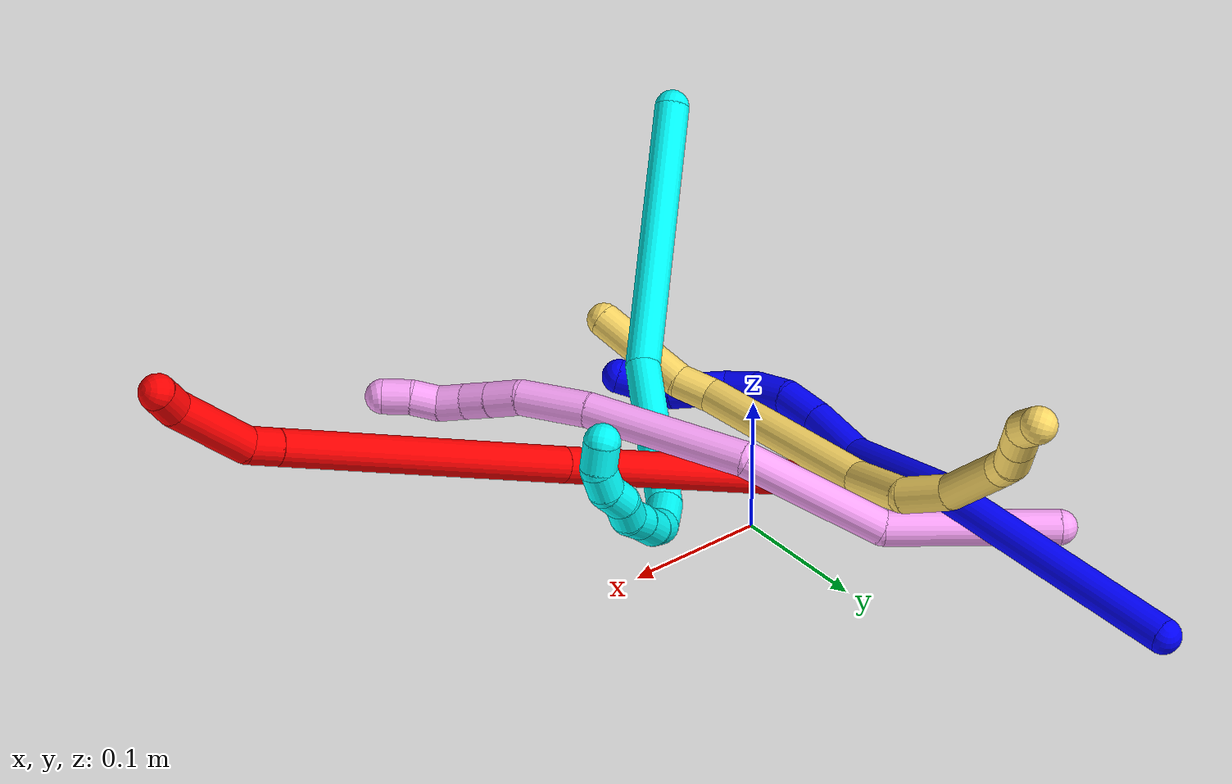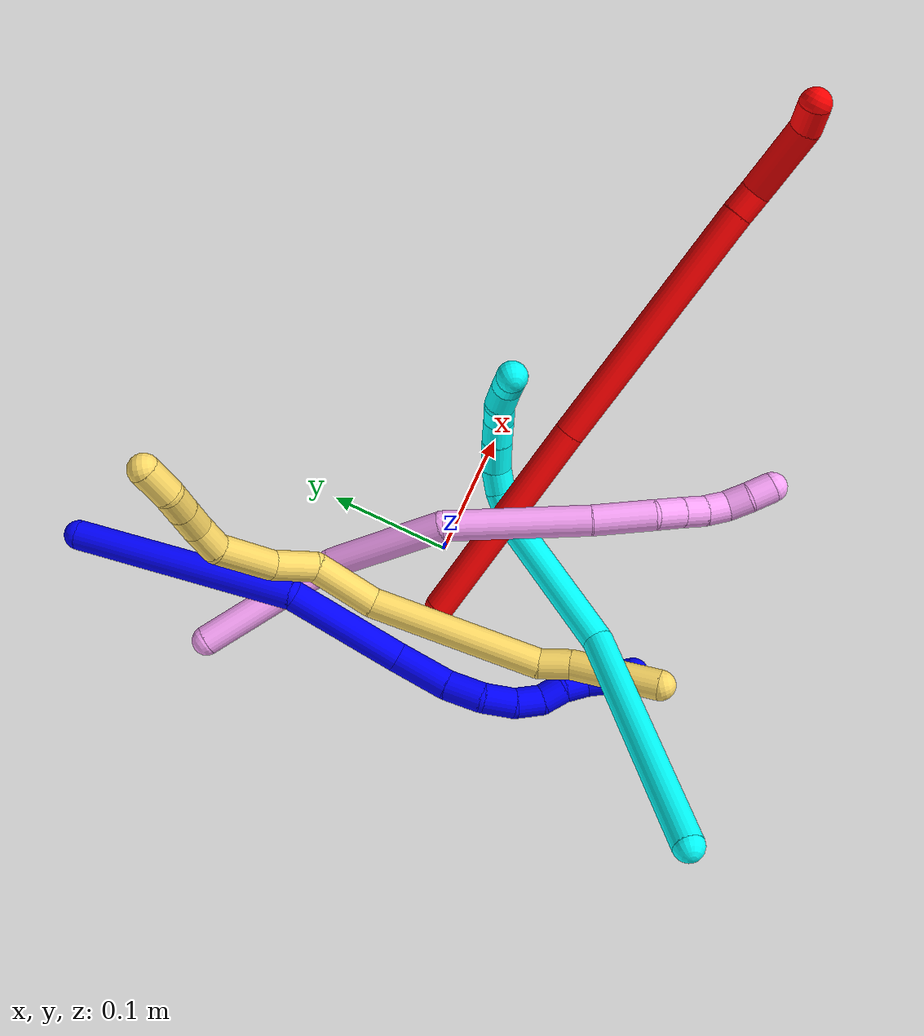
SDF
<sdf version="1.7">
 <world name="default">
  <plugin name="TubeGeneratorPlugin" filename="libtube_generator_plugin.so"/>
  <model name="photoneo_s_sensor">
   <static>1</static>
   <pose>0 0 2 1.57079 1.57079 3.14159</pose>
   <link name="link">
    <inertial><mass>0.1</mass></inertial>
    <sensor name="sensor" type="depth">
     <update_rate>30</update_rate>
     <camera>
      <horizontal_fov>1.22</horizontal_fov>
      <image><width>1920</width><height>1200</height><format>B8G8R8</format></image>
      <clip><near>0.1</near><far>4</far></clip>
      <depth_camera><output>points</output></depth_camera>
     </camera>
     <plugin name="camera_plugin" filename="libgazebo_ros_depth_camera.so">
      <baseline>0.2</baseline>
      <alwaysOn>1</alwaysOn>
      <updateRate>0.0</updateRate>
      <cameraName>camera_ir</cameraName>
      <imageTopicName>/camera/color/image_raw</imageTopicName>
      <cameraInfoTopicName>/camera/color/camera_info</cameraInfoTopicName>
      <depthImageTopicName>/camera/depth/image_raw</depthImageTopicName>
      <depthImageCameraInfoTopicName>/camera/depth/camera_info</depthImageCameraInfoTopicName>
      <pointCloudTopicName>/camera/depth/points</pointCloudTopicName>
      <frameName>fr_optical</frameName>
      <pointCloudCutoff>0.1</pointCloudCutoff>
      <pointCloudCutoffMax>2.0</pointCloudCutoffMax>
      <distortionK1>0</distortionK1>
      <distortionK2>0</distortionK2>
      <distortionK3>0</distortionK3>
      <distortionT1>0</distortionT1>
      <distortionT2>0</distortionT2>
      <CxPrime>0</CxPrime>
      <Cx>0</Cx>
      <Cy>0</Cy>
      <focalLength>0</focalLength>
      <hackBaseline>0</hackBaseline>
     </plugin>
    </sensor>
   </link>
  </model>
  <gravity>0 0 -9.8</gravity>
  <magnetic_field>6e-06 2.3e-05 -4.2e-05</magnetic_field>
  <atmosphere type="adiabatic"/>
  <physics name="default_physics" default="0" type="ode">
   <max_step_size>0.003</max_step_size>
   <real_time_factor>1</real_time_factor>
   <real_time_update_rate>1000</real_time_update_rate>
   <max_contacts>10000</max_contacts>
   <ode>
    <solver>
     <type>quick</type>
     <iters>100</iters>
     <sor>1.3</sor>
     <use_dynamic_moi_rescaling>0</use_dynamic_moi_rescaling>
    </solver>
    <constraints>
     <contact_max_correcting_vel>0</contact_max_correcting_vel>
     <contact_surface_layer>0.001</contact_surface_layer>
     <cfm>0</cfm>
     <erp>0.2</erp>
    </constraints>
   </ode>
  </physics>
  <scene><ambient>0.4 0.4 0.4 1</ambient><background>0.7 0.7 0.7 1</background><shadows>0</shadows></scene>
  <audio><device>default</device></audio>
  <spherical_coordinates>
   <surface_model>EARTH_WGS84</surface_model>
   <latitude_deg>0</latitude_deg>
   <longitude_deg>0</longitude_deg>
   <elevation>0</elevation>
   <heading_deg>0</heading_deg>
  </spherical_coordinates>
  <model name="bin">
   <static>1</static>
   <link name="bottom">
    <collision name="collision-bottom">
     <pose>0 0 -0.01 0 -0 0</pose>
     <geometry><box><size>0.8 0.6 0.02</size></box></geometry>
     <surface>
      <friction><ode><mu>100</mu><mu2>100</mu2></ode></friction>
      <contact><collide_bitmask>65535</collide_bitmask></contact>
     </surface>
    </collision>
   </link>
   <link name="west_wall">
    <collision name="collision-west_wall">
     <pose>-0.41 0 0.1 0 -0 0</pose>
     <geometry><box><size>0.02 0.6 0.2</size></box></geometry>
     <surface>
      <friction><ode><mu>100</mu><mu2>100</mu2></ode></friction>
      <contact><collide_bitmask>65535</collide_bitmask></contact>
     </surface>
    </collision>
   </link>
   <link name="east_wall">
    <collision name="collision-east_wall">
     <pose>0.41 0 0.1 0 -0 0</pose>
     <geometry><box><size>0.02 0.6 0.2</size></box></geometry>
     <surface>
      <friction><ode><mu>100</mu><mu2>100</mu2></ode></friction>
      <contact><collide_bitmask>65535</collide_bitmask></contact>
     </surface>
    </collision>
   </link>
   <link name="south_wall">
    <collision name="collision-south_wall">
     <pose>0 -0.31 0.1 0 -0 0</pose>
     <geometry><box><size>0.8 0.02 0.2</size></box></geometry>
     <surface>
      <friction><ode><mu>100</mu><mu2>100</mu2></ode></friction>
      <contact><collide_bitmask>65535</collide_bitmask></contact>
     </surface>
    </collision>
   </link>
   <link name="north_wall">
    <collision name="collision-north_wall">
     <pose>0 0.31 0.1 0 -0 0</pose>
     <geometry><box><size>0.8 0.02 0.2</size></box></geometry>
     <surface>
      <friction><ode><mu>100</mu><mu2>100</mu2></ode></friction>
      <contact><collide_bitmask>65535</collide_bitmask></contact>
     </surface>
    </collision>
   </link>
  </model>
  <model name="1">
   <static>0</static>
   <link name="1">
    <collision name="collision-cylinder-e_1_1_4">
     <pose>0.021934 -0.08818 -0.027343 1.87148 0.23326 0.315351</pose>
     <geometry><cylinder><radius>0.0125</radius><length>0.189783</length></cylinder></geometry>
     <surface>
      <friction><ode><mu>1.16</mu><mu2>1.16</mu2><slip1>0</slip1><slip2>0</slip2></ode></friction>
      <contact><ode><kp>1e+06</kp><kd>1</kd><max_vel>0</max_vel><min_depth>0.001</min_depth></ode></contact>
     </surface>
    </collision>
    <visual name="visual-cylinder-e_1_1_4">
     <pose>0.021934 -0.08818 -0.027343 1.87148 0.23326 0.315351</pose>
     <geometry><cylinder><radius>0.0125</radius><length>0.189783</length></cylinder></geometry>
     <material><ambient>0 0 1 1</ambient></material>
    </visual>
    <collision name="collision-cylinder-e_2_4_5">
     <pose>0.043896 -0.213903 -0.088982 2.31102 0.000548 0.001243</pose>
     <geometry><cylinder><radius>0.0125</radius><length>0.101701</length></cylinder></geometry>
     <surface>
      <friction><ode><mu>1.16</mu><mu2>1.16</mu2><slip1>0</slip1><slip2>0</slip2></ode></friction>
      <contact><ode><kp>1e+06</kp><kd>1</kd><max_vel>0</max_vel><min_depth>0.001</min_depth></ode></contact>
     </surface>
    </collision>
    <visual name="visual-cylinder-e_2_4_5">
     <pose>0.043896 -0.213903 -0.088982 2.31102 0.000548 0.001243</pose>
     <geometry><cylinder><radius>0.0125</radius><length>0.101701</length></cylinder></geometry>
     <material><ambient>0 0 1 1</ambient></material>
    </visual>
    <collision name="collision-cylinder-e_3_5_6">
     <pose>0.0441 -0.27351 -0.131873 1.94223 0.007431 0.01087</pose>
     <geometry><cylinder><radius>0.0125</radius><length>0.047357</length></cylinder></geometry>
     <surface>
      <friction><ode><mu>1.16</mu><mu2>1.16</mu2><slip1>0</slip1><slip2>0</slip2></ode></friction>
      <contact><ode><kp>1e+06</kp><kd>1</kd><max_vel>0</max_vel><min_depth>0.001</min_depth></ode></contact>
     </surface>
    </collision>
    <visual name="visual-cylinder-e_3_5_6">
     <pose>0.0441 -0.27351 -0.131873 1.94223 0.007431 0.01087</pose>
     <geometry><cylinder><radius>0.0125</radius><length>0.047357</length></cylinder></geometry>
     <material><ambient>0 0 1 1</ambient></material>
    </visual>
    <collision name="collision-cylinder-e_4_6_7">
     <pose>0.0469 -0.310041 -0.145344 1.89596 0.170215 0.236478</pose>
     <geometry><cylinder><radius>0.0125</radius><length>0.030983</length></cylinder></geometry>
     <surface>
      <friction><ode><mu>1.16</mu><mu2>1.16</mu2><slip1>0</slip1><slip2>0</slip2></ode></friction>
      <contact><ode><kp>1e+06</kp><kd>1</kd><max_vel>0</max_vel><min_depth>0.001</min_depth></ode></contact>
     </surface>
    </collision>
    <visual name="visual-cylinder-e_4_6_7">
     <pose>0.0469 -0.310041 -0.145344 1.89596 0.170215 0.236478</pose>
     <geometry><cylinder><radius>0.0125</radius><length>0.030983</length></cylinder></geometry>
     <material><ambient>0 0 1 1</ambient></material>
    </visual>
    <collision name="collision-cylinder-e_5_7_8">
     <pose>0.054135 -0.334996 -0.157087 2.15042 0.352472 0.636458</pose>
     <geometry><cylinder><radius>0.0125</radius><length>0.026712</length></cylinder></geometry>
     <surface>
      <friction><ode><mu>1.16</mu><mu2>1.16</mu2><slip1>0</slip1><slip2>0</slip2></ode></friction>
      <contact><ode><kp>1e+06</kp><kd>1</kd><max_vel>0</max_vel><min_depth>0.001</min_depth></ode></contact>
     </surface>
    </collision>
    <visual name="visual-cylinder-e_5_7_8">
     <pose>0.054135 -0.334996 -0.157087 2.15042 0.352472 0.636458</pose>
     <geometry><cylinder><radius>0.0125</radius><length>0.026712</length></cylinder></geometry>
     <material><ambient>0 0 1 1</ambient></material>
    </visual>
    <collision name="collision-cylinder-e_6_8_9">
     <pose>0.065545 -0.352681 -0.169701 2.24477 0.635835 1.19983</pose>
     <geometry><cylinder><radius>0.0125</radius><length>0.022897</length></cylinder></geometry>
     <surface>
      <friction><ode><mu>1.16</mu><mu2>1.16</mu2><slip1>0</slip1><slip2>0</slip2></ode></friction>
      <contact><ode><kp>1e+06</kp><kd>1</kd><max_vel>0</max_vel><min_depth>0.001</min_depth></ode></contact>
     </surface>
    </collision>
    <visual name="visual-cylinder-e_6_8_9">
     <pose>0.065545 -0.352681 -0.169701 2.24477 0.635835 1.19983</pose>
     <geometry><cylinder><radius>0.0125</radius><length>0.022897</length></cylinder></geometry>
     <material><ambient>0 0 1 1</ambient></material>
    </visual>
    <collision name="collision-cylinder-e_7_9_10">
     <pose>0.081036 -0.364557 -0.177826 2.04076 1.02768 1.48721</pose>
     <geometry><cylinder><radius>0.0125</radius><length>0.020309</length></cylinder></geometry>
     <surface>
      <friction><ode><mu>1.16</mu><mu2>1.16</mu2><slip1>0</slip1><slip2>0</slip2></ode></friction>
      <contact><ode><kp>1e+06</kp><kd>1</kd><max_vel>0</max_vel><min_depth>0.001</min_depth></ode></contact>
     </surface>
    </collision>
    <visual name="visual-cylinder-e_7_9_10">
     <pose>0.081036 -0.364557 -0.177826 2.04076 1.02768 1.48721</pose>
     <geometry><cylinder><radius>0.0125</radius><length>0.020309</length></cylinder></geometry>
     <material><ambient>0 0 1 1</ambient></material>
    </visual>
    <collision name="collision-cylinder-e_8_10_11">
     <pose>0.096667 -0.374709 -0.184918 2.28186 0.76512 1.4407</pose>
     <geometry><cylinder><radius>0.0125</radius><length>0.020031</length></cylinder></geometry>
     <surface>
      <friction><ode><mu>1.16</mu><mu2>1.16</mu2><slip1>0</slip1><slip2>0</slip2></ode></friction>
      <contact><ode><kp>1e+06</kp><kd>1</kd><max_vel>0</max_vel><min_depth>0.001</min_depth></ode></contact>
     </surface>
    </collision>
    <visual name="visual-cylinder-e_8_10_11">
     <pose>0.096667 -0.374709 -0.184918 2.28186 0.76512 1.4407</pose>
     <geometry><cylinder><radius>0.0125</radius><length>0.020031</length></cylinder></geometry>
     <material><ambient>0 0 1 1</ambient></material>
    </visual>
    <collision name="collision-cylinder-e_9_11_12">
     <pose>0.109636 -0.387915 -0.192003 1.86822 0.640805 0.843691</pose>
     <geometry><cylinder><radius>0.0125</radius><length>0.020179</length></cylinder></geometry>
     <surface>
      <friction><ode><mu>1.16</mu><mu2>1.16</mu2><slip1>0</slip1><slip2>0</slip2></ode></friction>
      <contact><ode><kp>1e+06</kp><kd>1</kd><max_vel>0</max_vel><min_depth>0.001</min_depth></ode></contact>
     </surface>
    </collision>
    <visual name="visual-cylinder-e_9_11_12">
     <pose>0.109636 -0.387915 -0.192003 1.86822 0.640805 0.843691</pose>
     <geometry><cylinder><radius>0.0125</radius><length>0.020179</length></cylinder></geometry>
     <material><ambient>0 0 1 1</ambient></material>
    </visual>
    <collision name="collision-cylinder-e_10_12_2">
     <pose>0.122308 -0.40308 -0.19545 1.71475 0.72408 0.824976</pose>
     <geometry><cylinder><radius>0.0125</radius><length>0.020048</length></cylinder></geometry>
     <surface>
      <friction><ode><mu>1.16</mu><mu2>1.16</mu2><slip1>0</slip1><slip2>0</slip2></ode></friction>
      <contact><ode><kp>1e+06</kp><kd>1</kd><max_vel>0</max_vel><min_depth>0.001</min_depth></ode></contact>
     </surface>
    </collision>
    <visual name="visual-cylinder-e_10_12_2">
     <pose>0.122308 -0.40308 -0.19545 1.71475 0.72408 0.824976</pose>
     <geometry><cylinder><radius>0.0125</radius><length>0.020048</length></cylinder></geometry>
     <material><ambient>0 0 1 1</ambient></material>
    </visual>
    <collision name="collision-sphere-2">
     <pose>0.128948 -0.410511 -0.196527 0 -0 0</pose>
     <geometry><sphere><radius>0.0125</radius></sphere></geometry>
     <surface>
      <friction><ode><mu>1.16</mu><mu2>1.16</mu2><slip1>0</slip1><slip2>0</slip2></ode></friction>
      <contact><ode><kp>1e+06</kp><kd>1</kd><max_vel>0</max_vel><min_depth>0.001</min_depth></ode></contact>
     </surface>
    </collision>
    <visual name="visual-sphere-2">
     <pose>0.128948 -0.410511 -0.196527 0 -0 0</pose>
     <geometry><sphere><radius>0.0125</radius></sphere></geometry>
     <material><ambient>0 0 1 1</ambient></material>
    </visual>
    <collision name="collision-sphere-12">
     <pose>0.115668 -0.395648 -0.194373 0 -0 0</pose>
     <geometry><sphere><radius>0.0125</radius></sphere></geometry>
     <surface>
      <friction><ode><mu>1.16</mu><mu2>1.16</mu2><slip1>0</slip1><slip2>0</slip2></ode></friction>
      <contact><ode><kp>1e+06</kp><kd>1</kd><max_vel>0</max_vel><min_depth>0.001</min_depth></ode></contact>
     </surface>
    </collision>
    <visual name="visual-sphere-12">
     <pose>0.115668 -0.395648 -0.194373 0 -0 0</pose>
     <geometry><sphere><radius>0.0125</radius></sphere></geometry>
     <material><ambient>0 0 1 1</ambient></material>
    </visual>
    <collision name="collision-sphere-11">
     <pose>0.103604 -0.380183 -0.189632 0 -0 0</pose>
     <geometry><sphere><radius>0.0125</radius></sphere></geometry>
     <surface>
      <friction><ode><mu>1.16</mu><mu2>1.16</mu2><slip1>0</slip1><slip2>0</slip2></ode></friction>
      <contact><ode><kp>1e+06</kp><kd>1</kd><max_vel>0</max_vel><min_depth>0.001</min_depth></ode></contact>
     </surface>
    </collision>
    <visual name="visual-sphere-11">
     <pose>0.103604 -0.380183 -0.189632 0 -0 0</pose>
     <geometry><sphere><radius>0.0125</radius></sphere></geometry>
     <material><ambient>0 0 1 1</ambient></material>
    </visual>
    <collision name="collision-sphere-10">
     <pose>0.08973 -0.369236 -0.180203 0 -0 0</pose>
     <geometry><sphere><radius>0.0125</radius></sphere></geometry>
     <surface>
      <friction><ode><mu>1.16</mu><mu2>1.16</mu2><slip1>0</slip1><slip2>0</slip2></ode></friction>
      <contact><ode><kp>1e+06</kp><kd>1</kd><max_vel>0</max_vel><min_depth>0.001</min_depth></ode></contact>
     </surface>
    </collision>
    <visual name="visual-sphere-10">
     <pose>0.08973 -0.369236 -0.180203 0 -0 0</pose>
     <geometry><sphere><radius>0.0125</radius></sphere></geometry>
     <material><ambient>0 0 1 1</ambient></material>
    </visual>
    <collision name="collision-sphere-9">
     <pose>0.072343 -0.359878 -0.17545 0 -0 0</pose>
     <geometry><sphere><radius>0.0125</radius></sphere></geometry>
     <surface>
      <friction><ode><mu>1.16</mu><mu2>1.16</mu2><slip1>0</slip1><slip2>0</slip2></ode></friction>
      <contact><ode><kp>1e+06</kp><kd>1</kd><max_vel>0</max_vel><min_depth>0.001</min_depth></ode></contact>
     </surface>
    </collision>
    <visual name="visual-sphere-9">
     <pose>0.072343 -0.359878 -0.17545 0 -0 0</pose>
     <geometry><sphere><radius>0.0125</radius></sphere></geometry>
     <material><ambient>0 0 1 1</ambient></material>
    </visual>
    <collision name="collision-sphere-4">
     <pose>0.043868 -0.176359 -0.054686 0 -0 0</pose>
     <geometry><sphere><radius>0.0125</radius></sphere></geometry>
     <surface>
      <friction><ode><mu>1.16</mu><mu2>1.16</mu2><slip1>0</slip1><slip2>0</slip2></ode></friction>
      <contact><ode><kp>1e+06</kp><kd>1</kd><max_vel>0</max_vel><min_depth>0.001</min_depth></ode></contact>
     </surface>
    </collision>
    <visual name="visual-sphere-4">
     <pose>0.043868 -0.176359 -0.054686 0 -0 0</pose>
     <geometry><sphere><radius>0.0125</radius></sphere></geometry>
     <material><ambient>0 0 1 1</ambient></material>
    </visual>
    <collision name="collision-sphere-1">
     <geometry><sphere><radius>0.0125</radius></sphere></geometry>
     <surface>
      <friction><ode><mu>1.16</mu><mu2>1.16</mu2><slip1>0</slip1><slip2>0</slip2></ode></friction>
      <contact><ode><kp>1e+06</kp><kd>1</kd><max_vel>0</max_vel><min_depth>0.001</min_depth></ode></contact>
     </surface>
    </collision>
    <visual name="visual-sphere-1">
     <geometry><sphere><radius>0.0125</radius></sphere></geometry>
     <material><ambient>0 0 1 1</ambient></material>
    </visual>
    <collision name="collision-sphere-8">
     <pose>0.058746 -0.345484 -0.163953 0 -0 0</pose>
     <geometry><sphere><radius>0.0125</radius></sphere></geometry>
     <surface>
      <friction><ode><mu>1.16</mu><mu2>1.16</mu2><slip1>0</slip1><slip2>0</slip2></ode></friction>
      <contact><ode><kp>1e+06</kp><kd>1</kd><max_vel>0</max_vel><min_depth>0.001</min_depth></ode></contact>
     </surface>
    </collision>
    <visual name="visual-sphere-8">
     <pose>0.058746 -0.345484 -0.163953 0 -0 0</pose>
     <geometry><sphere><radius>0.0125</radius></sphere></geometry>
     <material><ambient>0 0 1 1</ambient></material>
    </visual>
    <collision name="collision-sphere-5">
     <pose>0.043924 -0.251446 -0.123279 0 -0 0</pose>
     <geometry><sphere><radius>0.0125</radius></sphere></geometry>
     <surface>
      <friction><ode><mu>1.16</mu><mu2>1.16</mu2><slip1>0</slip1><slip2>0</slip2></ode></friction>
      <contact><ode><kp>1e+06</kp><kd>1</kd><max_vel>0</max_vel><min_depth>0.001</min_depth></ode></contact>
     </surface>
    </collision>
    <visual name="visual-sphere-5">
     <pose>0.043924 -0.251446 -0.123279 0 -0 0</pose>
     <geometry><sphere><radius>0.0125</radius></sphere></geometry>
     <material><ambient>0 0 1 1</ambient></material>
    </visual>
    <collision name="collision-sphere-6">
     <pose>0.044276 -0.295573 -0.140467 0 -0 0</pose>
     <geometry><sphere><radius>0.0125</radius></sphere></geometry>
     <surface>
      <friction><ode><mu>1.16</mu><mu2>1.16</mu2><slip1>0</slip1><slip2>0</slip2></ode></friction>
      <contact><ode><kp>1e+06</kp><kd>1</kd><max_vel>0</max_vel><min_depth>0.001</min_depth></ode></contact>
     </surface>
    </collision>
    <visual name="visual-sphere-6">
     <pose>0.044276 -0.295573 -0.140467 0 -0 0</pose>
     <geometry><sphere><radius>0.0125</radius></sphere></geometry>
     <material><ambient>0 0 1 1</ambient></material>
    </visual>
    <collision name="collision-sphere-7">
     <pose>0.049525 -0.324508 -0.150222 0 -0 0</pose>
     <geometry><sphere><radius>0.0125</radius></sphere></geometry>
     <surface>
      <friction><ode><mu>1.16</mu><mu2>1.16</mu2><slip1>0</slip1><slip2>0</slip2></ode></friction>
      <contact><ode><kp>1e+06</kp><kd>1</kd><max_vel>0</max_vel><min_depth>0.001</min_depth></ode></contact>
     </surface>
    </collision>
    <visual name="visual-sphere-7">
     <pose>0.049525 -0.324508 -0.150222 0 -0 0</pose>
     <geometry><sphere><radius>0.0125</radius></sphere></geometry>
     <material><ambient>0 0 1 1</ambient></material>
    </visual>
    <inertial>
     <pose>0.046724 -0.217779 -0.096355 0 -0 0</pose>
     <mass>0.5</mass>
     <inertia>
      <ixx>0.000836</ixx>
      <ixy>0</ixy>
      <ixz>0</ixz>
      <iyy>-3.8e-05</iyy>
      <iyz>0</iyz>
      <izz>0.000469</izz>
     </inertia>
    </inertial>
   </link>
   <pose>-0.119352 0.279738 0.012337 -0.476734 0.057044 -0.082074</pose>
  </model>
  <model name="2">
   <static>0</static>
   <link name="2">
    <collision name="collision-cylinder-e_1_1_4">
     <pose>0.016838 -0.003649 0.089598 0.040701 0.185608 0.003789</pose>
     <geometry><cylinder><radius>0.0125</radius><length>0.182479</length></cylinder></geometry>
     <surface>
      <friction><ode><mu>1.16</mu><mu2>1.16</mu2><slip1>0</slip1><slip2>0</slip2></ode></friction>
      <contact><ode><kp>1e+06</kp><kd>1</kd><max_vel>0</max_vel><min_depth>0.001</min_depth></ode></contact>
     </surface>
    </collision>
    <visual name="visual-cylinder-e_1_1_4">
     <pose>0.016838 -0.003649 0.089598 0.040701 0.185608 0.003789</pose>
     <geometry><cylinder><radius>0.0125</radius><length>0.182479</length></cylinder></geometry>
     <material><ambient>1 0 0 1</ambient></material>
    </visual>
    <collision name="collision-cylinder-e_2_4_5">
     <pose>0.054227 -0.012598 0.283583 0.050736 0.194154 0.004942</pose>
     <geometry><cylinder><radius>0.0125</radius><length>0.213045</length></cylinder></geometry>
     <surface>
      <friction><ode><mu>1.16</mu><mu2>1.16</mu2><slip1>0</slip1><slip2>0</slip2></ode></friction>
      <contact><ode><kp>1e+06</kp><kd>1</kd><max_vel>0</max_vel><min_depth>0.001</min_depth></ode></contact>
     </surface>
    </collision>
    <visual name="visual-cylinder-e_2_4_5">
     <pose>0.054227 -0.012598 0.283583 0.050736 0.194154 0.004942</pose>
     <geometry><cylinder><radius>0.0125</radius><length>0.213045</length></cylinder></geometry>
     <material><ambient>1 0 0 1</ambient></material>
    </visual>
    <collision name="collision-cylinder-e_3_5_6">
     <pose>0.077257 -0.018692 0.398516 0.075031 0.230072 0.008674</pose>
     <geometry><cylinder><radius>0.0125</radius><length>0.021726</length></cylinder></geometry>
     <surface>
      <friction><ode><mu>1.16</mu><mu2>1.16</mu2><slip1>0</slip1><slip2>0</slip2></ode></friction>
      <contact><ode><kp>1e+06</kp><kd>1</kd><max_vel>0</max_vel><min_depth>0.001</min_depth></ode></contact>
     </surface>
    </collision>
    <visual name="visual-cylinder-e_3_5_6">
     <pose>0.077257 -0.018692 0.398516 0.075031 0.230072 0.008674</pose>
     <geometry><cylinder><radius>0.0125</radius><length>0.021726</length></cylinder></geometry>
     <material><ambient>1 0 0 1</ambient></material>
    </visual>
    <collision name="collision-cylinder-e_4_6_7">
     <pose>0.075902 -0.027301 0.438291 0.261329 -0.125984 -0.016577</pose>
     <geometry><cylinder><radius>0.0125</radius><length>0.060993</length></cylinder></geometry>
     <surface>
      <friction><ode><mu>1.16</mu><mu2>1.16</mu2><slip1>0</slip1><slip2>0</slip2></ode></friction>
      <contact><ode><kp>1e+06</kp><kd>1</kd><max_vel>0</max_vel><min_depth>0.001</min_depth></ode></contact>
     </surface>
    </collision>
    <visual name="visual-cylinder-e_4_6_7">
     <pose>0.075902 -0.027301 0.438291 0.261329 -0.125984 -0.016577</pose>
     <geometry><cylinder><radius>0.0125</radius><length>0.060993</length></cylinder></geometry>
     <material><ambient>1 0 0 1</ambient></material>
    </visual>
    <collision name="collision-cylinder-e_5_7_2">
     <pose>0.067057 -0.036655 0.47705 0.159932 -0.478965 -0.039129</pose>
     <geometry><cylinder><radius>0.0125</radius><length>0.021757</length></cylinder></geometry>
     <surface>
      <friction><ode><mu>1.16</mu><mu2>1.16</mu2><slip1>0</slip1><slip2>0</slip2></ode></friction>
      <contact><ode><kp>1e+06</kp><kd>1</kd><max_vel>0</max_vel><min_depth>0.001</min_depth></ode></contact>
     </surface>
    </collision>
    <visual name="visual-cylinder-e_5_7_2">
     <pose>0.067057 -0.036655 0.47705 0.159932 -0.478965 -0.039129</pose>
     <geometry><cylinder><radius>0.0125</radius><length>0.021757</length></cylinder></geometry>
     <material><ambient>1 0 0 1</ambient></material>
    </visual>
    <collision name="collision-sphere-2">
     <pose>0.062043 -0.038193 0.486581 0 -0 0</pose>
     <geometry><sphere><radius>0.0125</radius></sphere></geometry>
     <surface>
      <friction><ode><mu>1.16</mu><mu2>1.16</mu2><slip1>0</slip1><slip2>0</slip2></ode></friction>
      <contact><ode><kp>1e+06</kp><kd>1</kd><max_vel>0</max_vel><min_depth>0.001</min_depth></ode></contact>
     </surface>
    </collision>
    <visual name="visual-sphere-2">
     <pose>0.062043 -0.038193 0.486581 0 -0 0</pose>
     <geometry><sphere><radius>0.0125</radius></sphere></geometry>
     <material><ambient>1 0 0 1</ambient></material>
    </visual>
    <collision name="collision-sphere-7">
     <pose>0.07207 -0.035118 0.467518 0 -0 0</pose>
     <geometry><sphere><radius>0.0125</radius></sphere></geometry>
     <surface>
      <friction><ode><mu>1.16</mu><mu2>1.16</mu2><slip1>0</slip1><slip2>0</slip2></ode></friction>
      <contact><ode><kp>1e+06</kp><kd>1</kd><max_vel>0</max_vel><min_depth>0.001</min_depth></ode></contact>
     </surface>
    </collision>
    <visual name="visual-sphere-7">
     <pose>0.07207 -0.035118 0.467518 0 -0 0</pose>
     <geometry><sphere><radius>0.0125</radius></sphere></geometry>
     <material><ambient>1 0 0 1</ambient></material>
    </visual>
    <collision name="collision-sphere-6">
     <pose>0.079734 -0.019484 0.409063 0 -0 0</pose>
     <geometry><sphere><radius>0.0125</radius></sphere></geometry>
     <surface>
      <friction><ode><mu>1.16</mu><mu2>1.16</mu2><slip1>0</slip1><slip2>0</slip2></ode></friction>
      <contact><ode><kp>1e+06</kp><kd>1</kd><max_vel>0</max_vel><min_depth>0.001</min_depth></ode></contact>
     </surface>
    </collision>
    <visual name="visual-sphere-6">
     <pose>0.079734 -0.019484 0.409063 0 -0 0</pose>
     <geometry><sphere><radius>0.0125</radius></sphere></geometry>
     <material><ambient>1 0 0 1</ambient></material>
    </visual>
    <collision name="collision-sphere-5">
     <pose>0.074779 -0.017899 0.387969 0 -0 0</pose>
     <geometry><sphere><radius>0.0125</radius></sphere></geometry>
     <surface>
      <friction><ode><mu>1.16</mu><mu2>1.16</mu2><slip1>0</slip1><slip2>0</slip2></ode></friction>
      <contact><ode><kp>1e+06</kp><kd>1</kd><max_vel>0</max_vel><min_depth>0.001</min_depth></ode></contact>
     </surface>
    </collision>
    <visual name="visual-sphere-5">
     <pose>0.074779 -0.017899 0.387969 0 -0 0</pose>
     <geometry><sphere><radius>0.0125</radius></sphere></geometry>
     <material><ambient>1 0 0 1</ambient></material>
    </visual>
    <collision name="collision-sphere-1">
     <geometry><sphere><radius>0.0125</radius></sphere></geometry>
     <surface>
      <friction><ode><mu>1.16</mu><mu2>1.16</mu2><slip1>0</slip1><slip2>0</slip2></ode></friction>
      <contact><ode><kp>1e+06</kp><kd>1</kd><max_vel>0</max_vel><min_depth>0.001</min_depth></ode></contact>
     </surface>
    </collision>
    <visual name="visual-sphere-1">
     <geometry><sphere><radius>0.0125</radius></sphere></geometry>
     <material><ambient>1 0 0 1</ambient></material>
    </visual>
    <collision name="collision-sphere-4">
     <pose>0.033675 -0.007297 0.179196 0 -0 0</pose>
     <geometry><sphere><radius>0.0125</radius></sphere></geometry>
     <surface>
      <friction><ode><mu>1.16</mu><mu2>1.16</mu2><slip1>0</slip1><slip2>0</slip2></ode></friction>
      <contact><ode><kp>1e+06</kp><kd>1</kd><max_vel>0</max_vel><min_depth>0.001</min_depth></ode></contact>
     </surface>
    </collision>
    <visual name="visual-sphere-4">
     <pose>0.033675 -0.007297 0.179196 0 -0 0</pose>
     <geometry><sphere><radius>0.0125</radius></sphere></geometry>
     <material><ambient>1 0 0 1</ambient></material>
    </visual>
    <inertial>
     <pose>0.044785 -0.012437 0.245071 0 -0 0</pose>
     <mass>0.5</mass>
     <inertia>
      <ixx>0.001338</ixx>
      <ixy>0</ixy>
      <ixz>0</ixz>
      <iyy>0.001353</iyy>
      <iyz>0</iyz>
      <izz>-0.000144</izz>
     </inertia>
    </inertial>
   </link>
   <pose>-0.045713 -0.01738 0.011486 -0.827673 0.813011 -1.04041</pose>
  </model>
  <model name="3">
   <static>0</static>
   <link name="3">
    <collision name="collision-cylinder-e_1_1_4">
     <pose>-0.005636 0.009255 -0.098503 -3.04791 -0.056909 1.09134</pose>
     <geometry><cylinder><radius>0.0125</radius><length>0.198195</length></cylinder></geometry>
     <surface>
      <friction><ode><mu>1.16</mu><mu2>1.16</mu2><slip1>0</slip1><slip2>0</slip2></ode></friction>
      <contact><ode><kp>1e+06</kp><kd>1</kd><max_vel>0</max_vel><min_depth>0.001</min_depth></ode></contact>
     </surface>
    </collision>
    <visual name="visual-cylinder-e_1_1_4">
     <pose>-0.005636 0.009255 -0.098503 -3.04791 -0.056909 1.09134</pose>
     <geometry><cylinder><radius>0.0125</radius><length>0.198195</length></cylinder></geometry>
     <material><ambient>0.003922 1 0.996078 1</ambient></material>
    </visual>
    <collision name="collision-cylinder-e_2_4_5">
     <pose>-0.00883 0.048797 -0.2509 -2.62962 0.039489 -0.150612</pose>
     <geometry><cylinder><radius>0.0125</radius><length>0.123739</length></cylinder></geometry>
     <surface>
      <friction><ode><mu>1.16</mu><mu2>1.16</mu2><slip1>0</slip1><slip2>0</slip2></ode></friction>
      <contact><ode><kp>1e+06</kp><kd>1</kd><max_vel>0</max_vel><min_depth>0.001</min_depth></ode></contact>
     </surface>
    </collision>
    <visual name="visual-cylinder-e_2_4_5">
     <pose>-0.00883 0.048797 -0.2509 -2.62962 0.039489 -0.150612</pose>
     <geometry><cylinder><radius>0.0125</radius><length>0.123739</length></cylinder></geometry>
     <material><ambient>0.003922 1 0.996078 1</ambient></material>
    </visual>
    <collision name="collision-cylinder-e_3_5_6">
     <pose>0.000256 0.086806 -0.314841 -2.48619 0.482936 -1.25386</pose>
     <geometry><cylinder><radius>0.0125</radius><length>0.028615</length></cylinder></geometry>
     <surface>
      <friction><ode><mu>1.16</mu><mu2>1.16</mu2><slip1>0</slip1><slip2>0</slip2></ode></friction>
      <contact><ode><kp>1e+06</kp><kd>1</kd><max_vel>0</max_vel><min_depth>0.001</min_depth></ode></contact>
     </surface>
    </collision>
    <visual name="visual-cylinder-e_3_5_6">
     <pose>0.000256 0.086806 -0.314841 -2.48619 0.482936 -1.25386</pose>
     <geometry><cylinder><radius>0.0125</radius><length>0.028615</length></cylinder></geometry>
     <material><ambient>0.003922 1 0.996078 1</ambient></material>
    </visual>
    <collision name="collision-cylinder-e_4_6_7">
     <pose>0.01546 0.100808 -0.328613 -2.10646 0.864518 -1.36203</pose>
     <geometry><cylinder><radius>0.0125</radius><length>0.022501</length></cylinder></geometry>
     <surface>
      <friction><ode><mu>1.16</mu><mu2>1.16</mu2><slip1>0</slip1><slip2>0</slip2></ode></friction>
      <contact><ode><kp>1e+06</kp><kd>1</kd><max_vel>0</max_vel><min_depth>0.001</min_depth></ode></contact>
     </surface>
    </collision>
    <visual name="visual-cylinder-e_4_6_7">
     <pose>0.01546 0.100808 -0.328613 -2.10646 0.864518 -1.36203</pose>
     <geometry><cylinder><radius>0.0125</radius><length>0.022501</length></cylinder></geometry>
     <material><ambient>0.003922 1 0.996078 1</ambient></material>
    </visual>
    <collision name="collision-cylinder-e_5_7_8">
     <pose>0.035534 0.113024 -0.333895 -1.82699 1.08109 -1.32191</pose>
     <geometry><cylinder><radius>0.0125</radius><length>0.026098</length></cylinder></geometry>
     <surface>
      <friction><ode><mu>1.16</mu><mu2>1.16</mu2><slip1>0</slip1><slip2>0</slip2></ode></friction>
      <contact><ode><kp>1e+06</kp><kd>1</kd><max_vel>0</max_vel><min_depth>0.001</min_depth></ode></contact>
     </surface>
    </collision>
    <visual name="visual-cylinder-e_5_7_8">
     <pose>0.035534 0.113024 -0.333895 -1.82699 1.08109 -1.32191</pose>
     <geometry><cylinder><radius>0.0125</radius><length>0.026098</length></cylinder></geometry>
     <material><ambient>0.003922 1 0.996078 1</ambient></material>
    </visual>
    <collision name="collision-cylinder-e_6_8_9">
     <pose>0.056256 0.123103 -0.337199 -1.97019 1.1166 -1.51062</pose>
     <geometry><cylinder><radius>0.0125</radius><length>0.020491</length></cylinder></geometry>
     <surface>
      <friction><ode><mu>1.16</mu><mu2>1.16</mu2><slip1>0</slip1><slip2>0</slip2></ode></friction>
      <contact><ode><kp>1e+06</kp><kd>1</kd><max_vel>0</max_vel><min_depth>0.001</min_depth></ode></contact>
     </surface>
    </collision>
    <visual name="visual-cylinder-e_6_8_9">
     <pose>0.056256 0.123103 -0.337199 -1.97019 1.1166 -1.51062</pose>
     <geometry><cylinder><radius>0.0125</radius><length>0.020491</length></cylinder></geometry>
     <material><ambient>0.003922 1 0.996078 1</ambient></material>
    </visual>
    <collision name="collision-cylinder-e_7_9_10">
     <pose>0.073926 0.132318 -0.33659 -1.13608 0.986711 -0.661147</pose>
     <geometry><cylinder><radius>0.0125</radius><length>0.020291</length></cylinder></geometry>
     <surface>
      <friction><ode><mu>1.16</mu><mu2>1.16</mu2><slip1>0</slip1><slip2>0</slip2></ode></friction>
      <contact><ode><kp>1e+06</kp><kd>1</kd><max_vel>0</max_vel><min_depth>0.001</min_depth></ode></contact>
     </surface>
    </collision>
    <visual name="visual-cylinder-e_7_9_10">
     <pose>0.073926 0.132318 -0.33659 -1.13608 0.986711 -0.661147</pose>
     <geometry><cylinder><radius>0.0125</radius><length>0.020291</length></cylinder></geometry>
     <material><ambient>0.003922 1 0.996078 1</ambient></material>
    </visual>
    <collision name="collision-cylinder-e_8_10_11">
     <pose>0.092115 0.139697 -0.333686 -1.33717 1.33184 -1.11087</pose>
     <geometry><cylinder><radius>0.0125</radius><length>0.02002</length></cylinder></geometry>
     <surface>
      <friction><ode><mu>1.16</mu><mu2>1.16</mu2><slip1>0</slip1><slip2>0</slip2></ode></friction>
      <contact><ode><kp>1e+06</kp><kd>1</kd><max_vel>0</max_vel><min_depth>0.001</min_depth></ode></contact>
     </surface>
    </collision>
    <visual name="visual-cylinder-e_8_10_11">
     <pose>0.092115 0.139697 -0.333686 -1.33717 1.33184 -1.11087</pose>
     <geometry><cylinder><radius>0.0125</radius><length>0.02002</length></cylinder></geometry>
     <material><ambient>0.003922 1 0.996078 1</ambient></material>
    </visual>
    <collision name="collision-cylinder-e_9_11_12">
     <pose>0.110116 0.145369 -0.328601 -0.638452 0.971872 -0.345675</pose>
     <geometry><cylinder><radius>0.0125</radius><length>0.020039</length></cylinder></geometry>
     <surface>
      <friction><ode><mu>1.16</mu><mu2>1.16</mu2><slip1>0</slip1><slip2>0</slip2></ode></friction>
      <contact><ode><kp>1e+06</kp><kd>1</kd><max_vel>0</max_vel><min_depth>0.001</min_depth></ode></contact>
     </surface>
    </collision>
    <visual name="visual-cylinder-e_9_11_12">
     <pose>0.110116 0.145369 -0.328601 -0.638452 0.971872 -0.345675</pose>
     <geometry><cylinder><radius>0.0125</radius><length>0.020039</length></cylinder></geometry>
     <material><ambient>0.003922 1 0.996078 1</ambient></material>
    </visual>
    <collision name="collision-cylinder-e_10_12_2">
     <pose>0.123194 0.153272 -0.316551 -0.543188 0.500563 -0.14214</pose>
     <geometry><cylinder><radius>0.0125</radius><length>0.020012</length></cylinder></geometry>
     <surface>
      <friction><ode><mu>1.16</mu><mu2>1.16</mu2><slip1>0</slip1><slip2>0</slip2></ode></friction>
      <contact><ode><kp>1e+06</kp><kd>1</kd><max_vel>0</max_vel><min_depth>0.001</min_depth></ode></contact>
     </surface>
    </collision>
    <visual name="visual-cylinder-e_10_12_2">
     <pose>0.123194 0.153272 -0.316551 -0.543188 0.500563 -0.14214</pose>
     <geometry><cylinder><radius>0.0125</radius><length>0.020012</length></cylinder></geometry>
     <material><ambient>0.003922 1 0.996078 1</ambient></material>
    </visual>
    <collision name="collision-sphere-2">
     <pose>0.127996 0.157809 -0.309036 0 -0 0</pose>
     <geometry><sphere><radius>0.0125</radius></sphere></geometry>
     <surface>
      <friction><ode><mu>1.16</mu><mu2>1.16</mu2><slip1>0</slip1><slip2>0</slip2></ode></friction>
      <contact><ode><kp>1e+06</kp><kd>1</kd><max_vel>0</max_vel><min_depth>0.001</min_depth></ode></contact>
     </surface>
    </collision>
    <visual name="visual-sphere-2">
     <pose>0.127996 0.157809 -0.309036 0 -0 0</pose>
     <geometry><sphere><radius>0.0125</radius></sphere></geometry>
     <material><ambient>0.003922 1 0.996078 1</ambient></material>
    </visual>
    <collision name="collision-sphere-12">
     <pose>0.118392 0.148735 -0.324065 0 -0 0</pose>
     <geometry><sphere><radius>0.0125</radius></sphere></geometry>
     <surface>
      <friction><ode><mu>1.16</mu><mu2>1.16</mu2><slip1>0</slip1><slip2>0</slip2></ode></friction>
      <contact><ode><kp>1e+06</kp><kd>1</kd><max_vel>0</max_vel><min_depth>0.001</min_depth></ode></contact>
     </surface>
    </collision>
    <visual name="visual-sphere-12">
     <pose>0.118392 0.148735 -0.324065 0 -0 0</pose>
     <geometry><sphere><radius>0.0125</radius></sphere></geometry>
     <material><ambient>0.003922 1 0.996078 1</ambient></material>
    </visual>
    <collision name="collision-sphere-11">
     <pose>0.101841 0.142002 -0.333137 0 -0 0</pose>
     <geometry><sphere><radius>0.0125</radius></sphere></geometry>
     <surface>
      <friction><ode><mu>1.16</mu><mu2>1.16</mu2><slip1>0</slip1><slip2>0</slip2></ode></friction>
      <contact><ode><kp>1e+06</kp><kd>1</kd><max_vel>0</max_vel><min_depth>0.001</min_depth></ode></contact>
     </surface>
    </collision>
    <visual name="visual-sphere-11">
     <pose>0.101841 0.142002 -0.333137 0 -0 0</pose>
     <geometry><sphere><radius>0.0125</radius></sphere></geometry>
     <material><ambient>0.003922 1 0.996078 1</ambient></material>
    </visual>
    <collision name="collision-sphere-10">
     <pose>0.08239 0.137392 -0.334234 0 -0 0</pose>
     <geometry><sphere><radius>0.0125</radius></sphere></geometry>
     <surface>
      <friction><ode><mu>1.16</mu><mu2>1.16</mu2><slip1>0</slip1><slip2>0</slip2></ode></friction>
      <contact><ode><kp>1e+06</kp><kd>1</kd><max_vel>0</max_vel><min_depth>0.001</min_depth></ode></contact>
     </surface>
    </collision>
    <visual name="visual-sphere-10">
     <pose>0.08239 0.137392 -0.334234 0 -0 0</pose>
     <geometry><sphere><radius>0.0125</radius></sphere></geometry>
     <material><ambient>0.003922 1 0.996078 1</ambient></material>
    </visual>
    <collision name="collision-sphere-9">
     <pose>0.065462 0.127244 -0.338947 0 -0 0</pose>
     <geometry><sphere><radius>0.0125</radius></sphere></geometry>
     <surface>
      <friction><ode><mu>1.16</mu><mu2>1.16</mu2><slip1>0</slip1><slip2>0</slip2></ode></friction>
      <contact><ode><kp>1e+06</kp><kd>1</kd><max_vel>0</max_vel><min_depth>0.001</min_depth></ode></contact>
     </surface>
    </collision>
    <visual name="visual-sphere-9">
     <pose>0.065462 0.127244 -0.338947 0 -0 0</pose>
     <geometry><sphere><radius>0.0125</radius></sphere></geometry>
     <material><ambient>0.003922 1 0.996078 1</ambient></material>
    </visual>
    <collision name="collision-sphere-4">
     <pose>-0.011273 0.018511 -0.197006 0 -0 0</pose>
     <geometry><sphere><radius>0.0125</radius></sphere></geometry>
     <surface>
      <friction><ode><mu>1.16</mu><mu2>1.16</mu2><slip1>0</slip1><slip2>0</slip2></ode></friction>
      <contact><ode><kp>1e+06</kp><kd>1</kd><max_vel>0</max_vel><min_depth>0.001</min_depth></ode></contact>
     </surface>
    </collision>
    <visual name="visual-sphere-4">
     <pose>-0.011273 0.018511 -0.197006 0 -0 0</pose>
     <geometry><sphere><radius>0.0125</radius></sphere></geometry>
     <material><ambient>0.003922 1 0.996078 1</ambient></material>
    </visual>
    <collision name="collision-sphere-1">
     <geometry><sphere><radius>0.0125</radius></sphere></geometry>
     <surface>
      <friction><ode><mu>1.16</mu><mu2>1.16</mu2><slip1>0</slip1><slip2>0</slip2></ode></friction>
      <contact><ode><kp>1e+06</kp><kd>1</kd><max_vel>0</max_vel><min_depth>0.001</min_depth></ode></contact>
     </surface>
    </collision>
    <visual name="visual-sphere-1">
     <geometry><sphere><radius>0.0125</radius></sphere></geometry>
     <material><ambient>0.003922 1 0.996078 1</ambient></material>
    </visual>
    <collision name="collision-sphere-8">
     <pose>0.047049 0.118961 -0.335451 0 -0 0</pose>
     <geometry><sphere><radius>0.0125</radius></sphere></geometry>
     <surface>
      <friction><ode><mu>1.16</mu><mu2>1.16</mu2><slip1>0</slip1><slip2>0</slip2></ode></friction>
      <contact><ode><kp>1e+06</kp><kd>1</kd><max_vel>0</max_vel><min_depth>0.001</min_depth></ode></contact>
     </surface>
    </collision>
    <visual name="visual-sphere-8">
     <pose>0.047049 0.118961 -0.335451 0 -0 0</pose>
     <geometry><sphere><radius>0.0125</radius></sphere></geometry>
     <material><ambient>0.003922 1 0.996078 1</ambient></material>
    </visual>
    <collision name="collision-sphere-5">
     <pose>-0.006388 0.079083 -0.304795 0 -0 0</pose>
     <geometry><sphere><radius>0.0125</radius></sphere></geometry>
     <surface>
      <friction><ode><mu>1.16</mu><mu2>1.16</mu2><slip1>0</slip1><slip2>0</slip2></ode></friction>
      <contact><ode><kp>1e+06</kp><kd>1</kd><max_vel>0</max_vel><min_depth>0.001</min_depth></ode></contact>
     </surface>
    </collision>
    <visual name="visual-sphere-5">
     <pose>-0.006388 0.079083 -0.304795 0 -0 0</pose>
     <geometry><sphere><radius>0.0125</radius></sphere></geometry>
     <material><ambient>0.003922 1 0.996078 1</ambient></material>
    </visual>
    <collision name="collision-sphere-6">
     <pose>0.006901 0.094529 -0.324887 0 -0 0</pose>
     <geometry><sphere><radius>0.0125</radius></sphere></geometry>
     <surface>
      <friction><ode><mu>1.16</mu><mu2>1.16</mu2><slip1>0</slip1><slip2>0</slip2></ode></friction>
      <contact><ode><kp>1e+06</kp><kd>1</kd><max_vel>0</max_vel><min_depth>0.001</min_depth></ode></contact>
     </surface>
    </collision>
    <visual name="visual-sphere-6">
     <pose>0.006901 0.094529 -0.324887 0 -0 0</pose>
     <geometry><sphere><radius>0.0125</radius></sphere></geometry>
     <material><ambient>0.003922 1 0.996078 1</ambient></material>
    </visual>
    <collision name="collision-sphere-7">
     <pose>0.024019 0.107087 -0.33234 0 -0 0</pose>
     <geometry><sphere><radius>0.0125</radius></sphere></geometry>
     <surface>
      <friction><ode><mu>1.16</mu><mu2>1.16</mu2><slip1>0</slip1><slip2>0</slip2></ode></friction>
      <contact><ode><kp>1e+06</kp><kd>1</kd><max_vel>0</max_vel><min_depth>0.001</min_depth></ode></contact>
     </surface>
    </collision>
    <visual name="visual-sphere-7">
     <pose>0.024019 0.107087 -0.33234 0 -0 0</pose>
     <geometry><sphere><radius>0.0125</radius></sphere></geometry>
     <material><ambient>0.003922 1 0.996078 1</ambient></material>
    </visual>
    <inertial>
     <pose>0.016483 0.059117 -0.218051 0 -0 0</pose>
     <mass>0.5</mass>
     <inertia>
      <ixx>0.001028</ixx>
      <ixy>0</ixy>
      <ixz>0</ixz>
      <iyy>0.000134</iyy>
      <iyz>0</iyz>
      <izz>-0.000152</izz>
     </inertia>
    </inertial>
   </link>
   <pose>-0.128181 -0.24911 0.177984 0.597598 -0.676034 -0.206358</pose>
  </model>
  <model name="4">
   <static>0</static>
   <link name="4">
    <collision name="collision-cylinder-e_1_1_4">
     <pose>0.006272 -0.006898 -0.060333 3.02775 0.102923 1.46993</pose>
     <geometry><cylinder><radius>0.0125</radius><length>0.122099</length></cylinder></geometry>
     <surface>
      <friction><ode><mu>1.16</mu><mu2>1.16</mu2><slip1>0</slip1><slip2>0</slip2></ode></friction>
      <contact><ode><kp>1e+06</kp><kd>1</kd><max_vel>0</max_vel><min_depth>0.001</min_depth></ode></contact>
     </surface>
    </collision>
    <visual name="visual-cylinder-e_1_1_4">
     <pose>0.006272 -0.006898 -0.060333 3.02775 0.102923 1.46993</pose>
     <geometry><cylinder><radius>0.0125</radius><length>0.122099</length></cylinder></geometry>
     <material><ambient>1 0.65098 0.996078 1</ambient></material>
    </visual>
    <collision name="collision-cylinder-e_2_4_5">
     <pose>0.034747 -0.034566 -0.16373 2.69221 0.434761 1.53663</pose>
     <geometry><cylinder><radius>0.0125</radius><length>0.105428</length></cylinder></geometry>
     <surface>
      <friction><ode><mu>1.16</mu><mu2>1.16</mu2><slip1>0</slip1><slip2>0</slip2></ode></friction>
      <contact><ode><kp>1e+06</kp><kd>1</kd><max_vel>0</max_vel><min_depth>0.001</min_depth></ode></contact>
     </surface>
    </collision>
    <visual name="visual-cylinder-e_2_4_5">
     <pose>0.034747 -0.034566 -0.16373 2.69221 0.434761 1.53663</pose>
     <geometry><cylinder><radius>0.0125</radius><length>0.105428</length></cylinder></geometry>
     <material><ambient>1 0.65098 0.996078 1</ambient></material>
    </visual>
    <collision name="collision-cylinder-e_3_5_6">
     <pose>0.057949 -0.089899 -0.254629 2.51589 0.016923 0.052306</pose>
     <geometry><cylinder><radius>0.0125</radius><length>0.118049</length></cylinder></geometry>
     <surface>
      <friction><ode><mu>1.16</mu><mu2>1.16</mu2><slip1>0</slip1><slip2>0</slip2></ode></friction>
      <contact><ode><kp>1e+06</kp><kd>1</kd><max_vel>0</max_vel><min_depth>0.001</min_depth></ode></contact>
     </surface>
    </collision>
    <visual name="visual-cylinder-e_3_5_6">
     <pose>0.057949 -0.089899 -0.254629 2.51589 0.016923 0.052306</pose>
     <geometry><cylinder><radius>0.0125</radius><length>0.118049</length></cylinder></geometry>
     <material><ambient>1 0.65098 0.996078 1</ambient></material>
    </visual>
    <collision name="collision-cylinder-e_4_6_7">
     <pose>0.057169 -0.137725 -0.324039 2.59042 -0.070136 -0.246862</pose>
     <geometry><cylinder><radius>0.0125</radius><length>0.050775</length></cylinder></geometry>
     <surface>
      <friction><ode><mu>1.16</mu><mu2>1.16</mu2><slip1>0</slip1><slip2>0</slip2></ode></friction>
      <contact><ode><kp>1e+06</kp><kd>1</kd><max_vel>0</max_vel><min_depth>0.001</min_depth></ode></contact>
     </surface>
    </collision>
    <visual name="visual-cylinder-e_4_6_7">
     <pose>0.057169 -0.137725 -0.324039 2.59042 -0.070136 -0.246862</pose>
     <geometry><cylinder><radius>0.0125</radius><length>0.050775</length></cylinder></geometry>
     <material><ambient>1 0.65098 0.996078 1</ambient></material>
    </visual>
    <collision name="collision-cylinder-e_5_7_8">
     <pose>0.051531 -0.156083 -0.355514 2.6662 -0.333577 -1.21455</pose>
     <geometry><cylinder><radius>0.0125</radius><length>0.023569</length></cylinder></geometry>
     <surface>
      <friction><ode><mu>1.16</mu><mu2>1.16</mu2><slip1>0</slip1><slip2>0</slip2></ode></friction>
      <contact><ode><kp>1e+06</kp><kd>1</kd><max_vel>0</max_vel><min_depth>0.001</min_depth></ode></contact>
     </surface>
    </collision>
    <visual name="visual-cylinder-e_5_7_8">
     <pose>0.051531 -0.156083 -0.355514 2.6662 -0.333577 -1.21455</pose>
     <geometry><cylinder><radius>0.0125</radius><length>0.023569</length></cylinder></geometry>
     <material><ambient>1 0.65098 0.996078 1</ambient></material>
    </visual>
    <collision name="collision-cylinder-e_6_8_9">
     <pose>0.044362 -0.165707 -0.373694 2.64119 -0.337405 -1.17575</pose>
     <geometry><cylinder><radius>0.0125</radius><length>0.020002</length></cylinder></geometry>
     <surface>
      <friction><ode><mu>1.16</mu><mu2>1.16</mu2><slip1>0</slip1><slip2>0</slip2></ode></friction>
      <contact><ode><kp>1e+06</kp><kd>1</kd><max_vel>0</max_vel><min_depth>0.001</min_depth></ode></contact>
     </surface>
    </collision>
    <visual name="visual-cylinder-e_6_8_9">
     <pose>0.044362 -0.165707 -0.373694 2.64119 -0.337405 -1.17575</pose>
     <geometry><cylinder><radius>0.0125</radius><length>0.020002</length></cylinder></geometry>
     <material><ambient>1 0.65098 0.996078 1</ambient></material>
    </visual>
    <collision name="collision-cylinder-e_7_9_10">
     <pose>0.038585 -0.173817 -0.391005 2.76396 -0.248568 -1.15802</pose>
     <geometry><cylinder><radius>0.0125</radius><length>0.020047</length></cylinder></geometry>
     <surface>
      <friction><ode><mu>1.16</mu><mu2>1.16</mu2><slip1>0</slip1><slip2>0</slip2></ode></friction>
      <contact><ode><kp>1e+06</kp><kd>1</kd><max_vel>0</max_vel><min_depth>0.001</min_depth></ode></contact>
     </surface>
    </collision>
    <visual name="visual-cylinder-e_7_9_10">
     <pose>0.038585 -0.173817 -0.391005 2.76396 -0.248568 -1.15802</pose>
     <geometry><cylinder><radius>0.0125</radius><length>0.020047</length></cylinder></geometry>
     <material><ambient>1 0.65098 0.996078 1</ambient></material>
    </visual>
    <collision name="collision-cylinder-e_8_10_11">
     <pose>0.038237 -0.180535 -0.409294 2.81509 0.213324 1.15277</pose>
     <geometry><cylinder><radius>0.0125</radius><length>0.020003</length></cylinder></geometry>
     <surface>
      <friction><ode><mu>1.16</mu><mu2>1.16</mu2><slip1>0</slip1><slip2>0</slip2></ode></friction>
      <contact><ode><kp>1e+06</kp><kd>1</kd><max_vel>0</max_vel><min_depth>0.001</min_depth></ode></contact>
     </surface>
    </collision>
    <visual name="visual-cylinder-e_8_10_11">
     <pose>0.038237 -0.180535 -0.409294 2.81509 0.213324 1.15277</pose>
     <geometry><cylinder><radius>0.0125</radius><length>0.020003</length></cylinder></geometry>
     <material><ambient>1 0.65098 0.996078 1</ambient></material>
    </visual>
    <collision name="collision-cylinder-e_9_11_2">
     <pose>0.040691 -0.186045 -0.428275 2.90201 0.033604 0.277405</pose>
     <geometry><cylinder><radius>0.0125</radius><length>0.020028</length></cylinder></geometry>
     <surface>
      <friction><ode><mu>1.16</mu><mu2>1.16</mu2><slip1>0</slip1><slip2>0</slip2></ode></friction>
      <contact><ode><kp>1e+06</kp><kd>1</kd><max_vel>0</max_vel><min_depth>0.001</min_depth></ode></contact>
     </surface>
    </collision>
    <visual name="visual-cylinder-e_9_11_2">
     <pose>0.040691 -0.186045 -0.428275 2.90201 0.033604 0.277405</pose>
     <geometry><cylinder><radius>0.0125</radius><length>0.020028</length></cylinder></geometry>
     <material><ambient>1 0.65098 0.996078 1</ambient></material>
    </visual>
    <collision name="collision-sphere-2">
     <pose>0.041027 -0.18842 -0.437998 0 -0 0</pose>
     <geometry><sphere><radius>0.0125</radius></sphere></geometry>
     <surface>
      <friction><ode><mu>1.16</mu><mu2>1.16</mu2><slip1>0</slip1><slip2>0</slip2></ode></friction>
      <contact><ode><kp>1e+06</kp><kd>1</kd><max_vel>0</max_vel><min_depth>0.001</min_depth></ode></contact>
     </surface>
    </collision>
    <visual name="visual-sphere-2">
     <pose>0.041027 -0.18842 -0.437998 0 -0 0</pose>
     <geometry><sphere><radius>0.0125</radius></sphere></geometry>
     <material><ambient>1 0.65098 0.996078 1</ambient></material>
    </visual>
    <collision name="collision-sphere-11">
     <pose>0.040354 -0.18367 -0.418553 0 -0 0</pose>
     <geometry><sphere><radius>0.0125</radius></sphere></geometry>
     <surface>
      <friction><ode><mu>1.16</mu><mu2>1.16</mu2><slip1>0</slip1><slip2>0</slip2></ode></friction>
      <contact><ode><kp>1e+06</kp><kd>1</kd><max_vel>0</max_vel><min_depth>0.001</min_depth></ode></contact>
     </surface>
    </collision>
    <visual name="visual-sphere-11">
     <pose>0.040354 -0.18367 -0.418553 0 -0 0</pose>
     <geometry><sphere><radius>0.0125</radius></sphere></geometry>
     <material><ambient>1 0.65098 0.996078 1</ambient></material>
    </visual>
    <collision name="collision-sphere-10">
     <pose>0.036119 -0.177399 -0.400035 0 -0 0</pose>
     <geometry><sphere><radius>0.0125</radius></sphere></geometry>
     <surface>
      <friction><ode><mu>1.16</mu><mu2>1.16</mu2><slip1>0</slip1><slip2>0</slip2></ode></friction>
      <contact><ode><kp>1e+06</kp><kd>1</kd><max_vel>0</max_vel><min_depth>0.001</min_depth></ode></contact>
     </surface>
    </collision>
    <visual name="visual-sphere-10">
     <pose>0.036119 -0.177399 -0.400035 0 -0 0</pose>
     <geometry><sphere><radius>0.0125</radius></sphere></geometry>
     <material><ambient>1 0.65098 0.996078 1</ambient></material>
    </visual>
    <collision name="collision-sphere-9">
     <pose>0.041051 -0.170235 -0.381974 0 -0 0</pose>
     <geometry><sphere><radius>0.0125</radius></sphere></geometry>
     <surface>
      <friction><ode><mu>1.16</mu><mu2>1.16</mu2><slip1>0</slip1><slip2>0</slip2></ode></friction>
      <contact><ode><kp>1e+06</kp><kd>1</kd><max_vel>0</max_vel><min_depth>0.001</min_depth></ode></contact>
     </surface>
    </collision>
    <visual name="visual-sphere-9">
     <pose>0.041051 -0.170235 -0.381974 0 -0 0</pose>
     <geometry><sphere><radius>0.0125</radius></sphere></geometry>
     <material><ambient>1 0.65098 0.996078 1</ambient></material>
    </visual>
    <collision name="collision-sphere-4">
     <pose>0.012545 -0.013797 -0.120666 0 -0 0</pose>
     <geometry><sphere><radius>0.0125</radius></sphere></geometry>
     <surface>
      <friction><ode><mu>1.16</mu><mu2>1.16</mu2><slip1>0</slip1><slip2>0</slip2></ode></friction>
      <contact><ode><kp>1e+06</kp><kd>1</kd><max_vel>0</max_vel><min_depth>0.001</min_depth></ode></contact>
     </surface>
    </collision>
    <visual name="visual-sphere-4">
     <pose>0.012545 -0.013797 -0.120666 0 -0 0</pose>
     <geometry><sphere><radius>0.0125</radius></sphere></geometry>
     <material><ambient>1 0.65098 0.996078 1</ambient></material>
    </visual>
    <collision name="collision-sphere-1">
     <geometry><sphere><radius>0.0125</radius></sphere></geometry>
     <surface>
      <friction><ode><mu>1.16</mu><mu2>1.16</mu2><slip1>0</slip1><slip2>0</slip2></ode></friction>
      <contact><ode><kp>1e+06</kp><kd>1</kd><max_vel>0</max_vel><min_depth>0.001</min_depth></ode></contact>
     </surface>
    </collision>
    <visual name="visual-sphere-1">
     <geometry><sphere><radius>0.0125</radius></sphere></geometry>
     <material><ambient>1 0.65098 0.996078 1</ambient></material>
    </visual>
    <collision name="collision-sphere-8">
     <pose>0.047673 -0.16118 -0.365414 0 -0 0</pose>
     <geometry><sphere><radius>0.0125</radius></sphere></geometry>
     <surface>
      <friction><ode><mu>1.16</mu><mu2>1.16</mu2><slip1>0</slip1><slip2>0</slip2></ode></friction>
      <contact><ode><kp>1e+06</kp><kd>1</kd><max_vel>0</max_vel><min_depth>0.001</min_depth></ode></contact>
     </surface>
    </collision>
    <visual name="visual-sphere-8">
     <pose>0.047673 -0.16118 -0.365414 0 -0 0</pose>
     <geometry><sphere><radius>0.0125</radius></sphere></geometry>
     <material><ambient>1 0.65098 0.996078 1</ambient></material>
    </visual>
    <collision name="collision-sphere-5">
     <pose>0.05695 -0.055335 -0.206793 0 -0 0</pose>
     <geometry><sphere><radius>0.0125</radius></sphere></geometry>
     <surface>
      <friction><ode><mu>1.16</mu><mu2>1.16</mu2><slip1>0</slip1><slip2>0</slip2></ode></friction>
      <contact><ode><kp>1e+06</kp><kd>1</kd><max_vel>0</max_vel><min_depth>0.001</min_depth></ode></contact>
     </surface>
    </collision>
    <visual name="visual-sphere-5">
     <pose>0.05695 -0.055335 -0.206793 0 -0 0</pose>
     <geometry><sphere><radius>0.0125</radius></sphere></geometry>
     <material><ambient>1 0.65098 0.996078 1</ambient></material>
    </visual>
    <collision name="collision-sphere-6">
     <pose>0.058948 -0.124462 -0.302464 0 -0 0</pose>
     <geometry><sphere><radius>0.0125</radius></sphere></geometry>
     <surface>
      <friction><ode><mu>1.16</mu><mu2>1.16</mu2><slip1>0</slip1><slip2>0</slip2></ode></friction>
      <contact><ode><kp>1e+06</kp><kd>1</kd><max_vel>0</max_vel><min_depth>0.001</min_depth></ode></contact>
     </surface>
    </collision>
    <visual name="visual-sphere-6">
     <pose>0.058948 -0.124462 -0.302464 0 -0 0</pose>
     <geometry><sphere><radius>0.0125</radius></sphere></geometry>
     <material><ambient>1 0.65098 0.996078 1</ambient></material>
    </visual>
    <collision name="collision-sphere-7">
     <pose>0.05539 -0.150987 -0.345614 0 -0 0</pose>
     <geometry><sphere><radius>0.0125</radius></sphere></geometry>
     <surface>
      <friction><ode><mu>1.16</mu><mu2>1.16</mu2><slip1>0</slip1><slip2>0</slip2></ode></friction>
      <contact><ode><kp>1e+06</kp><kd>1</kd><max_vel>0</max_vel><min_depth>0.001</min_depth></ode></contact>
     </surface>
    </collision>
    <visual name="visual-sphere-7">
     <pose>0.05539 -0.150987 -0.345614 0 -0 0</pose>
     <geometry><sphere><radius>0.0125</radius></sphere></geometry>
     <material><ambient>1 0.65098 0.996078 1</ambient></material>
    </visual>
    <inertial>
     <pose>0.037256 -0.079814 -0.223194 0 -0 0</pose>
     <mass>0.5</mass>
     <inertia>
      <ixx>0.000428</ixx>
      <ixy>0</ixy>
      <ixz>0</ixz>
      <iyy>0.000108</iyy>
      <iyz>0</iyz>
      <izz>5.7e-05</izz>
     </inertia>
    </inertial>
   </link>
   <pose>-0.152775 0.145409 0.011448 -1.22338 -1.37752 0.740443</pose>
  </model>
  <model name="5">
   <static>0</static>
   <link name="5">
    <collision name="collision-cylinder-e_1_1_4">
     <pose>0.010447 0.010792 -0.033918 -2.83355 0.285491 -1.49371</pose>
     <geometry><cylinder><radius>0.0125</radius><length>0.074191</length></cylinder></geometry>
     <surface>
      <friction><ode><mu>1.16</mu><mu2>1.16</mu2><slip1>0</slip1><slip2>0</slip2></ode></friction>
      <contact><ode><kp>1e+06</kp><kd>1</kd><max_vel>0</max_vel><min_depth>0.001</min_depth></ode></contact>
     </surface>
    </collision>
    <visual name="visual-cylinder-e_1_1_4">
     <pose>0.010447 0.010792 -0.033918 -2.83355 0.285491 -1.49371</pose>
     <geometry><cylinder><radius>0.0125</radius><length>0.074191</length></cylinder></geometry>
     <material><ambient>1 0.858824 0.4 1</ambient></material>
    </visual>
    <collision name="collision-cylinder-e_2_4_5">
     <pose>0.02151 0.024422 -0.080826 -2.92649 0.046275 -0.422296</pose>
     <geometry><cylinder><radius>0.0125</radius><length>0.02662</length></cylinder></geometry>
     <surface>
      <friction><ode><mu>1.16</mu><mu2>1.16</mu2><slip1>0</slip1><slip2>0</slip2></ode></friction>
      <contact><ode><kp>1e+06</kp><kd>1</kd><max_vel>0</max_vel><min_depth>0.001</min_depth></ode></contact>
     </surface>
    </collision>
    <visual name="visual-cylinder-e_2_4_5">
     <pose>0.02151 0.024422 -0.080826 -2.92649 0.046275 -0.422296</pose>
     <geometry><cylinder><radius>0.0125</radius><length>0.02662</length></cylinder></geometry>
     <material><ambient>1 0.858824 0.4 1</ambient></material>
    </visual>
    <collision name="collision-cylinder-e_3_5_6">
     <pose>0.025977 0.066424 -0.154521 -2.56864 0.053263 -0.180361</pose>
     <geometry><cylinder><radius>0.0125</radius><length>0.14469</length></cylinder></geometry>
     <surface>
      <friction><ode><mu>1.16</mu><mu2>1.16</mu2><slip1>0</slip1><slip2>0</slip2></ode></friction>
      <contact><ode><kp>1e+06</kp><kd>1</kd><max_vel>0</max_vel><min_depth>0.001</min_depth></ode></contact>
     </surface>
    </collision>
    <visual name="visual-cylinder-e_3_5_6">
     <pose>0.025977 0.066424 -0.154521 -2.56864 0.053263 -0.180361</pose>
     <geometry><cylinder><radius>0.0125</radius><length>0.14469</length></cylinder></geometry>
     <material><ambient>1 0.858824 0.4 1</ambient></material>
    </visual>
    <collision name="collision-cylinder-e_4_6_7">
     <pose>0.026225 0.127308 -0.23259 -2.24518 -0.128878 0.2668</pose>
     <geometry><cylinder><radius>0.0125</radius><length>0.056079</length></cylinder></geometry>
     <surface>
      <friction><ode><mu>1.16</mu><mu2>1.16</mu2><slip1>0</slip1><slip2>0</slip2></ode></friction>
      <contact><ode><kp>1e+06</kp><kd>1</kd><max_vel>0</max_vel><min_depth>0.001</min_depth></ode></contact>
     </surface>
    </collision>
    <visual name="visual-cylinder-e_4_6_7">
     <pose>0.026225 0.127308 -0.23259 -2.24518 -0.128878 0.2668</pose>
     <geometry><cylinder><radius>0.0125</radius><length>0.056079</length></cylinder></geometry>
     <material><ambient>1 0.858824 0.4 1</ambient></material>
    </visual>
    <collision name="collision-cylinder-e_5_7_8">
     <pose>0.014928 0.156641 -0.265048 -2.67442 -0.427038 1.47805</pose>
     <geometry><cylinder><radius>0.0125</radius><length>0.037148</length></cylinder></geometry>
     <surface>
      <friction><ode><mu>1.16</mu><mu2>1.16</mu2><slip1>0</slip1><slip2>0</slip2></ode></friction>
      <contact><ode><kp>1e+06</kp><kd>1</kd><max_vel>0</max_vel><min_depth>0.001</min_depth></ode></contact>
     </surface>
    </collision>
    <visual name="visual-cylinder-e_5_7_8">
     <pose>0.014928 0.156641 -0.265048 -2.67442 -0.427038 1.47805</pose>
     <geometry><cylinder><radius>0.0125</radius><length>0.037148</length></cylinder></geometry>
     <material><ambient>1 0.858824 0.4 1</ambient></material>
    </visual>
    <collision name="collision-cylinder-e_6_8_9">
     <pose>-0.009003 0.181864 -0.29403 -2.2386 -0.626709 1.17818</pose>
     <geometry><cylinder><radius>0.0125</radius><length>0.055376</length></cylinder></geometry>
     <surface>
      <friction><ode><mu>1.16</mu><mu2>1.16</mu2><slip1>0</slip1><slip2>0</slip2></ode></friction>
      <contact><ode><kp>1e+06</kp><kd>1</kd><max_vel>0</max_vel><min_depth>0.001</min_depth></ode></contact>
     </surface>
    </collision>
    <visual name="visual-cylinder-e_6_8_9">
     <pose>-0.009003 0.181864 -0.29403 -2.2386 -0.626709 1.17818</pose>
     <geometry><cylinder><radius>0.0125</radius><length>0.055376</length></cylinder></geometry>
     <material><ambient>1 0.858824 0.4 1</ambient></material>
    </visual>
    <collision name="collision-cylinder-e_7_9_10">
     <pose>-0.030442 0.211384 -0.310828 -1.81046 -0.401095 0.506739</pose>
     <geometry><cylinder><radius>0.0125</radius><length>0.026637</length></cylinder></geometry>
     <surface>
      <friction><ode><mu>1.16</mu><mu2>1.16</mu2><slip1>0</slip1><slip2>0</slip2></ode></friction>
      <contact><ode><kp>1e+06</kp><kd>1</kd><max_vel>0</max_vel><min_depth>0.001</min_depth></ode></contact>
     </surface>
    </collision>
    <visual name="visual-cylinder-e_7_9_10">
     <pose>-0.030442 0.211384 -0.310828 -1.81046 -0.401095 0.506739</pose>
     <geometry><cylinder><radius>0.0125</radius><length>0.026637</length></cylinder></geometry>
     <material><ambient>1 0.858824 0.4 1</ambient></material>
    </visual>
    <collision name="collision-cylinder-e_8_10_11">
     <pose>-0.043524 0.234013 -0.314076 -1.6023 -0.633905 0.652807</pose>
     <geometry><cylinder><radius>0.0125</radius><length>0.026618</length></cylinder></geometry>
     <surface>
      <friction><ode><mu>1.16</mu><mu2>1.16</mu2><slip1>0</slip1><slip2>0</slip2></ode></friction>
      <contact><ode><kp>1e+06</kp><kd>1</kd><max_vel>0</max_vel><min_depth>0.001</min_depth></ode></contact>
     </surface>
    </collision>
    <visual name="visual-cylinder-e_8_10_11">
     <pose>-0.043524 0.234013 -0.314076 -1.6023 -0.633905 0.652807</pose>
     <geometry><cylinder><radius>0.0125</radius><length>0.026618</length></cylinder></geometry>
     <material><ambient>1 0.858824 0.4 1</ambient></material>
    </visual>
    <collision name="collision-cylinder-e_9_11_12">
     <pose>-0.058611 0.254427 -0.314665 -1.59663 -0.638819 0.654385</pose>
     <geometry><cylinder><radius>0.0125</radius><length>0.024165</length></cylinder></geometry>
     <surface>
      <friction><ode><mu>1.16</mu><mu2>1.16</mu2><slip1>0</slip1><slip2>0</slip2></ode></friction>
      <contact><ode><kp>1e+06</kp><kd>1</kd><max_vel>0</max_vel><min_depth>0.001</min_depth></ode></contact>
     </surface>
    </collision>
    <visual name="visual-cylinder-e_9_11_12">
     <pose>-0.058611 0.254427 -0.314665 -1.59663 -0.638819 0.654385</pose>
     <geometry><cylinder><radius>0.0125</radius><length>0.024165</length></cylinder></geometry>
     <material><ambient>1 0.858824 0.4 1</ambient></material>
    </visual>
    <collision name="collision-cylinder-e_10_12_2">
     <pose>-0.070606 0.276863 -0.319096 -1.88791 -0.343147 0.469648</pose>
     <geometry><cylinder><radius>0.0125</radius><length>0.028475</length></cylinder></geometry>
     <surface>
      <friction><ode><mu>1.16</mu><mu2>1.16</mu2><slip1>0</slip1><slip2>0</slip2></ode></friction>
      <contact><ode><kp>1e+06</kp><kd>1</kd><max_vel>0</max_vel><min_depth>0.001</min_depth></ode></contact>
     </surface>
    </collision>
    <visual name="visual-cylinder-e_10_12_2">
     <pose>-0.070606 0.276863 -0.319096 -1.88791 -0.343147 0.469648</pose>
     <geometry><cylinder><radius>0.0125</radius><length>0.028475</length></cylinder></geometry>
     <material><ambient>1 0.858824 0.4 1</ambient></material>
    </visual>
    <collision name="collision-sphere-2">
     <pose>-0.075396 0.289602 -0.323277 0 -0 0</pose>
     <geometry><sphere><radius>0.0125</radius></sphere></geometry>
     <surface>
      <friction><ode><mu>1.16</mu><mu2>1.16</mu2><slip1>0</slip1><slip2>0</slip2></ode></friction>
      <contact><ode><kp>1e+06</kp><kd>1</kd><max_vel>0</max_vel><min_depth>0.001</min_depth></ode></contact>
     </surface>
    </collision>
    <visual name="visual-sphere-2">
     <pose>-0.075396 0.289602 -0.323277 0 -0 0</pose>
     <geometry><sphere><radius>0.0125</radius></sphere></geometry>
     <material><ambient>1 0.858824 0.4 1</ambient></material>
    </visual>
    <collision name="collision-sphere-12">
     <pose>-0.065816 0.264124 -0.314915 0 -0 0</pose>
     <geometry><sphere><radius>0.0125</radius></sphere></geometry>
     <surface>
      <friction><ode><mu>1.16</mu><mu2>1.16</mu2><slip1>0</slip1><slip2>0</slip2></ode></friction>
      <contact><ode><kp>1e+06</kp><kd>1</kd><max_vel>0</max_vel><min_depth>0.001</min_depth></ode></contact>
     </surface>
    </collision>
    <visual name="visual-sphere-12">
     <pose>-0.065816 0.264124 -0.314915 0 -0 0</pose>
     <geometry><sphere><radius>0.0125</radius></sphere></geometry>
     <material><ambient>1 0.858824 0.4 1</ambient></material>
    </visual>
    <collision name="collision-sphere-11">
     <pose>-0.051407 0.244731 -0.314414 0 -0 0</pose>
     <geometry><sphere><radius>0.0125</radius></sphere></geometry>
     <surface>
      <friction><ode><mu>1.16</mu><mu2>1.16</mu2><slip1>0</slip1><slip2>0</slip2></ode></friction>
      <contact><ode><kp>1e+06</kp><kd>1</kd><max_vel>0</max_vel><min_depth>0.001</min_depth></ode></contact>
     </surface>
    </collision>
    <visual name="visual-sphere-11">
     <pose>-0.051407 0.244731 -0.314414 0 -0 0</pose>
     <geometry><sphere><radius>0.0125</radius></sphere></geometry>
     <material><ambient>1 0.858824 0.4 1</ambient></material>
    </visual>
    <collision name="collision-sphere-10">
     <pose>-0.035642 0.223295 -0.313739 0 -0 0</pose>
     <geometry><sphere><radius>0.0125</radius></sphere></geometry>
     <surface>
      <friction><ode><mu>1.16</mu><mu2>1.16</mu2><slip1>0</slip1><slip2>0</slip2></ode></friction>
      <contact><ode><kp>1e+06</kp><kd>1</kd><max_vel>0</max_vel><min_depth>0.001</min_depth></ode></contact>
     </surface>
    </collision>
    <visual name="visual-sphere-10">
     <pose>-0.035642 0.223295 -0.313739 0 -0 0</pose>
     <geometry><sphere><radius>0.0125</radius></sphere></geometry>
     <material><ambient>1 0.858824 0.4 1</ambient></material>
    </visual>
    <collision name="collision-sphere-9">
     <pose>-0.025242 0.199472 -0.307917 0 -0 0</pose>
     <geometry><sphere><radius>0.0125</radius></sphere></geometry>
     <surface>
      <friction><ode><mu>1.16</mu><mu2>1.16</mu2><slip1>0</slip1><slip2>0</slip2></ode></friction>
      <contact><ode><kp>1e+06</kp><kd>1</kd><max_vel>0</max_vel><min_depth>0.001</min_depth></ode></contact>
     </surface>
    </collision>
    <visual name="visual-sphere-9">
     <pose>-0.025242 0.199472 -0.307917 0 -0 0</pose>
     <geometry><sphere><radius>0.0125</radius></sphere></geometry>
     <material><ambient>1 0.858824 0.4 1</ambient></material>
    </visual>
    <collision name="collision-sphere-4">
     <pose>0.020894 0.021584 -0.067837 0 -0 0</pose>
     <geometry><sphere><radius>0.0125</radius></sphere></geometry>
     <surface>
      <friction><ode><mu>1.16</mu><mu2>1.16</mu2><slip1>0</slip1><slip2>0</slip2></ode></friction>
      <contact><ode><kp>1e+06</kp><kd>1</kd><max_vel>0</max_vel><min_depth>0.001</min_depth></ode></contact>
     </surface>
    </collision>
    <visual name="visual-sphere-4">
     <pose>0.020894 0.021584 -0.067837 0 -0 0</pose>
     <geometry><sphere><radius>0.0125</radius></sphere></geometry>
     <material><ambient>1 0.858824 0.4 1</ambient></material>
    </visual>
    <collision name="collision-sphere-1">
     <geometry><sphere><radius>0.0125</radius></sphere></geometry>
     <surface>
      <friction><ode><mu>1.16</mu><mu2>1.16</mu2><slip1>0</slip1><slip2>0</slip2></ode></friction>
      <contact><ode><kp>1e+06</kp><kd>1</kd><max_vel>0</max_vel><min_depth>0.001</min_depth></ode></contact>
     </surface>
    </collision>
    <visual name="visual-sphere-1">
     <geometry><sphere><radius>0.0125</radius></sphere></geometry>
     <material><ambient>1 0.858824 0.4 1</ambient></material>
    </visual>
    <collision name="collision-sphere-8">
     <pose>0.007235 0.164255 -0.280142 0 -0 0</pose>
     <geometry><sphere><radius>0.0125</radius></sphere></geometry>
     <surface>
      <friction><ode><mu>1.16</mu><mu2>1.16</mu2><slip1>0</slip1><slip2>0</slip2></ode></friction>
      <contact><ode><kp>1e+06</kp><kd>1</kd><max_vel>0</max_vel><min_depth>0.001</min_depth></ode></contact>
     </surface>
    </collision>
    <visual name="visual-sphere-8">
     <pose>0.007235 0.164255 -0.280142 0 -0 0</pose>
     <geometry><sphere><radius>0.0125</radius></sphere></geometry>
     <material><ambient>1 0.858824 0.4 1</ambient></material>
    </visual>
    <collision name="collision-sphere-5">
     <pose>0.022126 0.02726 -0.093815 0 -0 0</pose>
     <geometry><sphere><radius>0.0125</radius></sphere></geometry>
     <surface>
      <friction><ode><mu>1.16</mu><mu2>1.16</mu2><slip1>0</slip1><slip2>0</slip2></ode></friction>
      <contact><ode><kp>1e+06</kp><kd>1</kd><max_vel>0</max_vel><min_depth>0.001</min_depth></ode></contact>
     </surface>
    </collision>
    <visual name="visual-sphere-5">
     <pose>0.022126 0.02726 -0.093815 0 -0 0</pose>
     <geometry><sphere><radius>0.0125</radius></sphere></geometry>
     <material><ambient>1 0.858824 0.4 1</ambient></material>
    </visual>
    <collision name="collision-sphere-6">
     <pose>0.029829 0.105588 -0.215227 0 -0 0</pose>
     <geometry><sphere><radius>0.0125</radius></sphere></geometry>
     <surface>
      <friction><ode><mu>1.16</mu><mu2>1.16</mu2><slip1>0</slip1><slip2>0</slip2></ode></friction>
      <contact><ode><kp>1e+06</kp><kd>1</kd><max_vel>0</max_vel><min_depth>0.001</min_depth></ode></contact>
     </surface>
    </collision>
    <visual name="visual-sphere-6">
     <pose>0.029829 0.105588 -0.215227 0 -0 0</pose>
     <geometry><sphere><radius>0.0125</radius></sphere></geometry>
     <material><ambient>1 0.858824 0.4 1</ambient></material>
    </visual>
    <collision name="collision-sphere-7">
     <pose>0.022621 0.149028 -0.249953 0 -0 0</pose>
     <geometry><sphere><radius>0.0125</radius></sphere></geometry>
     <surface>
      <friction><ode><mu>1.16</mu><mu2>1.16</mu2><slip1>0</slip1><slip2>0</slip2></ode></friction>
      <contact><ode><kp>1e+06</kp><kd>1</kd><max_vel>0</max_vel><min_depth>0.001</min_depth></ode></contact>
     </surface>
    </collision>
    <visual name="visual-sphere-7">
     <pose>0.022621 0.149028 -0.249953 0 -0 0</pose>
     <geometry><sphere><radius>0.0125</radius></sphere></geometry>
     <material><ambient>1 0.858824 0.4 1</ambient></material>
    </visual>
    <inertial>
     <pose>0.002473 0.119965 -0.199055 0 -0 0</pose>
     <mass>0.5</mass>
     <inertia>
      <ixx>0.000226</ixx>
      <ixy>0</ixy>
      <ixz>0</ixz>
      <iyy>-0.000252</iyy>
      <iyz>0</iyz>
      <izz>-0.000216</izz>
     </inertia>
    </inertial>
   </link>
   <pose>-0.028774 -0.20269 0.057264 1.0988 1.08669 0.202198</pose>
  </model>
 </world>
</sdf>
